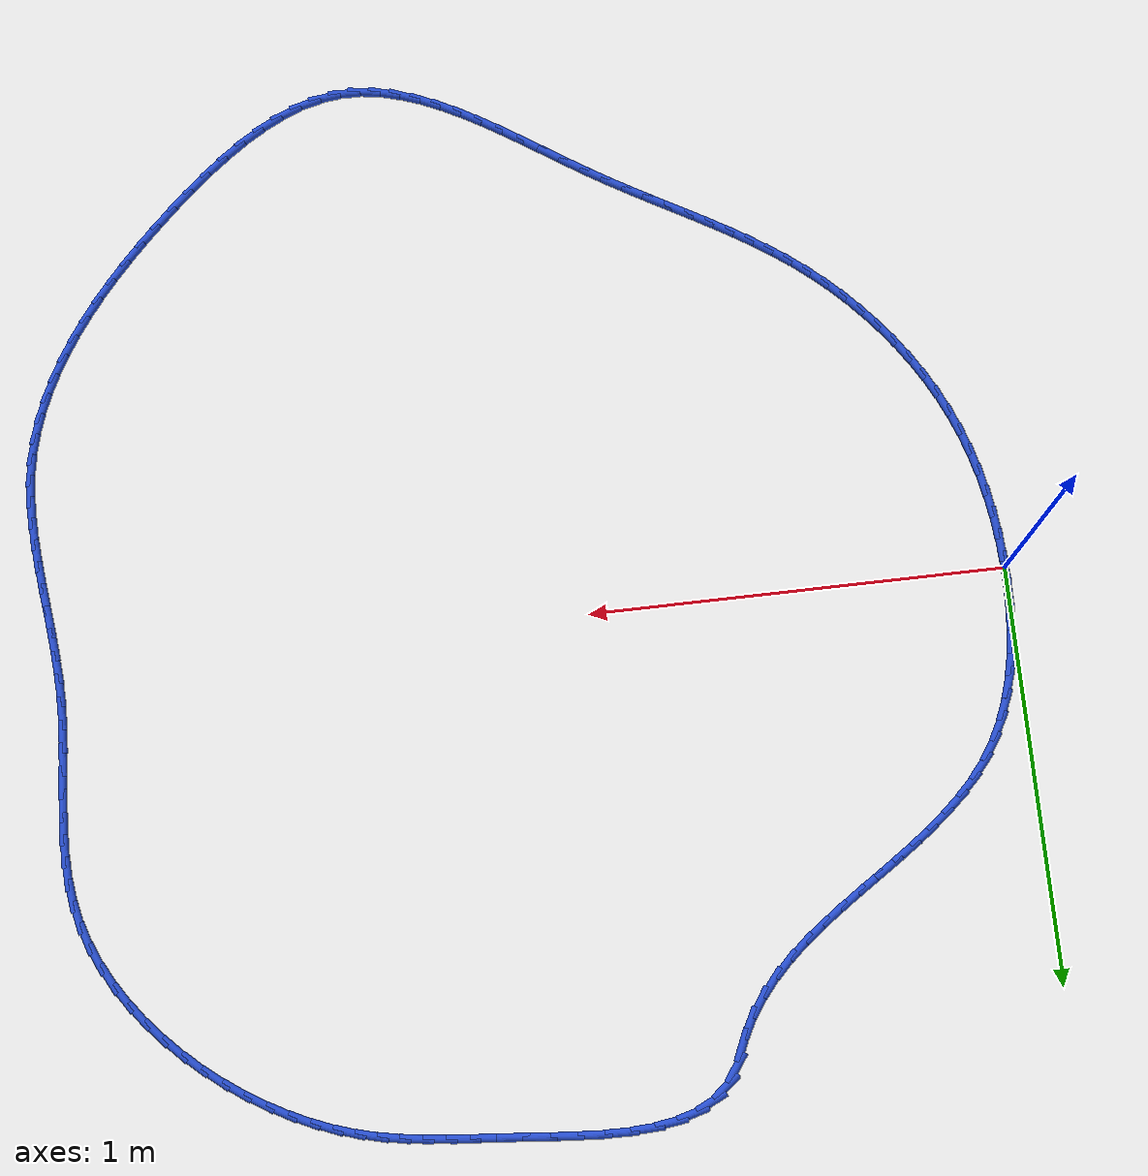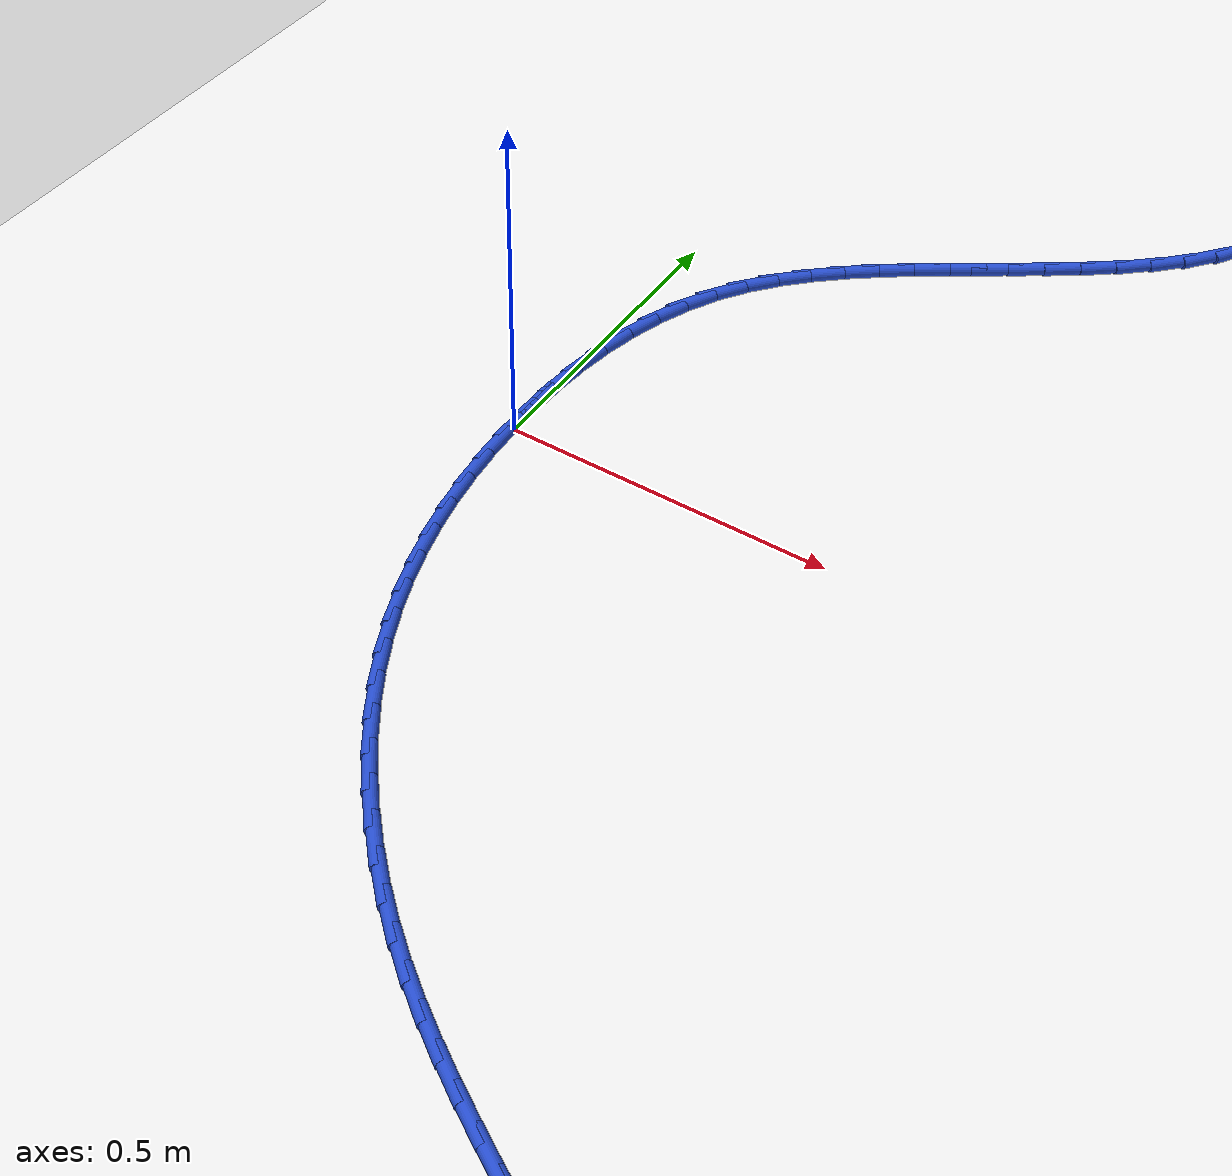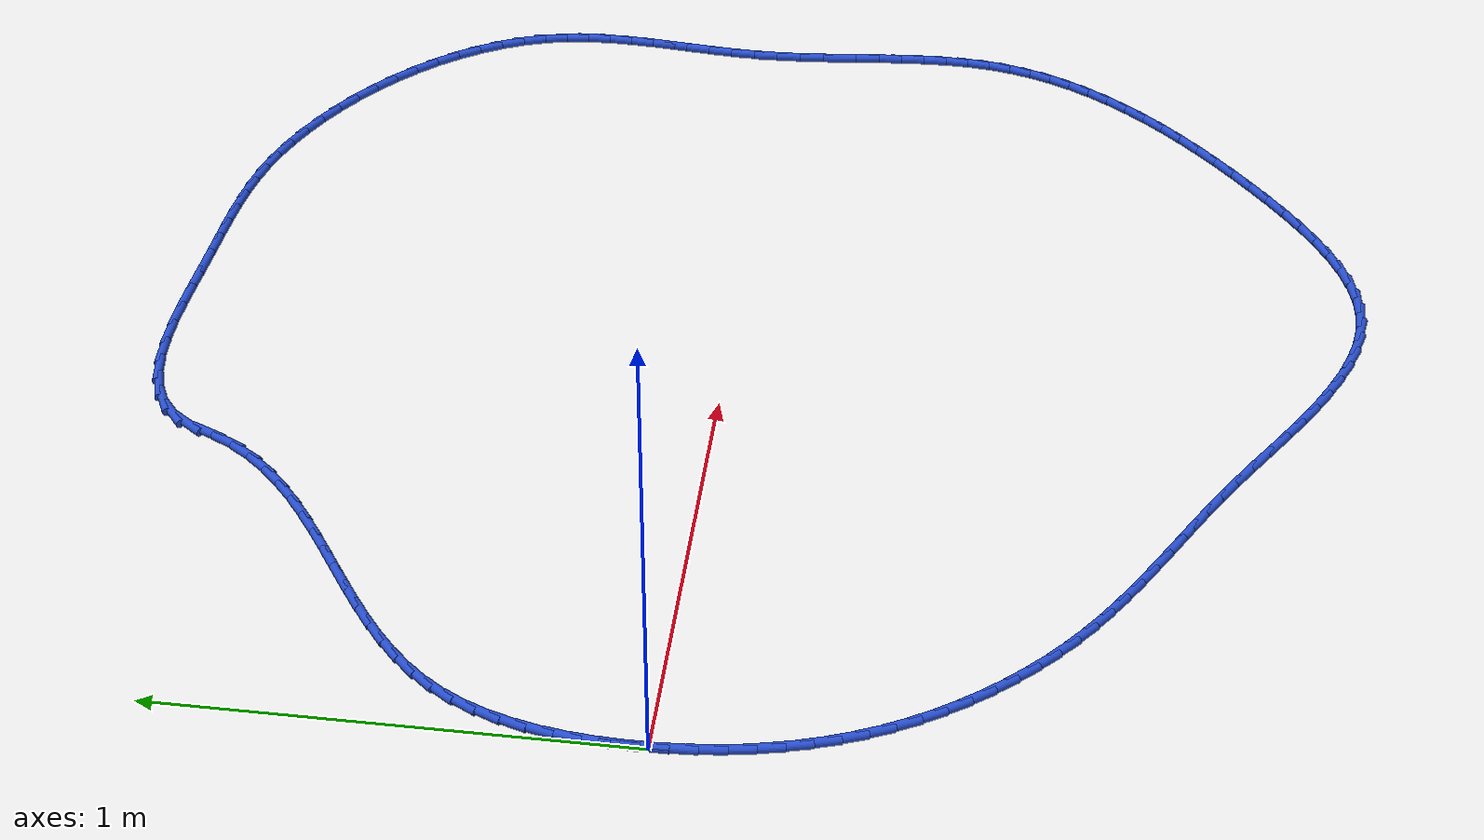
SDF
<sdf version="1.6">
 <world name="default">
  <light name="sun" type="directional">
   <pose>0 0 10 0 -0 0</pose>
   <diffuse>0.8 0.8 0.8 1</diffuse>
   <specular>0.2 0.2 0.2 1</specular>
   <attenuation>
    <range>1000</range>
    <constant>0.9</constant>
    <linear>0.01</linear>
    <quadratic>0.001</quadratic>
   </attenuation>
   <direction>-0.5 0.1 -0.9</direction>
  </light>
  <model name="ground_plane">
   <static>1</static>
   <link name="link">
    <collision name="collision">
     <geometry><plane><normal>0 0 1</normal><size>100 100</size></plane></geometry>
     <surface><friction><ode><mu>100</mu><mu2>50</mu2></ode></friction></surface>
    </collision>
    <visual name="visual">
     <cast_shadows>0</cast_shadows>
     <geometry><plane><normal>0 0 1</normal><size>100 100</size></plane></geometry>
     <material>
      <script><uri>file://media/materials/scripts/gazebo.material</uri><name>Gazebo/WhiteGlow</name></script>
     </material>
    </visual>
   </link>
  </model>
  <gravity>0 0 -9.8</gravity>
  <magnetic_field>6e-06 2.3e-05 -4.2e-05</magnetic_field>
  <atmosphere type="adiabatic"/>
  <physics name="default_physics" default="0" type="ode">
   <max_step_size>0.001</max_step_size>
   <real_time_factor>1</real_time_factor>
   <real_time_update_rate>1000</real_time_update_rate>
  </physics>
  <scene><ambient>0.4 0.4 0.4 1</ambient><background>0.7 0.7 0.7 1</background><shadows>1</shadows></scene>
  <spherical_coordinates>
   <surface_model>EARTH_WGS84</surface_model>
   <latitude_deg>0</latitude_deg>
   <longitude_deg>0</longitude_deg>
   <elevation>0</elevation>
   <heading_deg>0</heading_deg>
  </spherical_coordinates>
  <model name="line">
   <link name="link_0">
    <pose>-6.938893903907228e-18 -1.3877787807814457e-16 0.01 0 1.57 1.5702225282403262</pose>
    <collision name="collision">
     <geometry><cylinder><radius>0.01</radius><length>0.08</length></cylinder></geometry>
    </collision>
    <visual name="visual">
     <material>
      <script><name>Gazebo/Blue</name><uri>file://media/materials/scripts/gazebo.material</uri></script>
     </material>
     <geometry><cylinder><radius>0.01</radius><length>0.08</length></cylinder></geometry>
    </visual>
   </link>
   <link name="link_1">
    <pose>3.2122297887926364e-05 0.05598183213727158 0.01 0 1.57 1.5219617204032692</pose>
    <collision name="collision">
     <geometry><cylinder><radius>0.01</radius><length>0.08</length></cylinder></geometry>
    </collision>
    <visual name="visual">
     <material>
      <script><name>Gazebo/Blue</name><uri>file://media/materials/scripts/gazebo.material</uri></script>
     </material>
     <geometry><cylinder><radius>0.01</radius><length>0.08</length></cylinder></geometry>
    </visual>
   </link>
   <link name="link_2">
    <pose>0.0027720591368958205 0.1120436827521187 0.01 0 1.57 1.4680645423843748</pose>
    <collision name="collision">
     <geometry><cylinder><radius>0.01</radius><length>0.08</length></cylinder></geometry>
    </collision>
    <visual name="visual">
     <material>
      <script><name>Gazebo/Blue</name><uri>file://media/materials/scripts/gazebo.material</uri></script>
     </material>
     <geometry><cylinder><radius>0.01</radius><length>0.08</length></cylinder></geometry>
    </visual>
   </link>
   <link name="link_3">
    <pose>0.008510602290415246 0.1677065053002968 0.01 0 1.57 1.4074748132549735</pose>
    <collision name="collision">
     <geometry><cylinder><radius>0.01</radius><length>0.08</length></cylinder></geometry>
    </collision>
    <visual name="visual">
     <material>
      <script><name>Gazebo/Blue</name><uri>file://media/materials/scripts/gazebo.material</uri></script>
     </material>
     <geometry><cylinder><radius>0.01</radius><length>0.08</length></cylinder></geometry>
    </visual>
   </link>
   <link name="link_4">
    <pose>0.017538543531837758 0.22249125323756133 0.01 0 1.57 1.3390508978373714</pose>
    <collision name="collision">
     <geometry><cylinder><radius>0.01</radius><length>0.08</length></cylinder></geometry>
    </collision>
    <visual name="visual">
     <material>
      <script><name>Gazebo/Blue</name><uri>file://media/materials/scripts/gazebo.material</uri></script>
     </material>
     <geometry><cylinder><radius>0.01</radius><length>0.08</length></cylinder></geometry>
    </visual>
   </link>
   <link name="link_5">
    <pose>0.030146674634554928 0.2759188800196679 0.01 0 1.57 1.261623660727146</pose>
    <collision name="collision">
     <geometry><cylinder><radius>0.01</radius><length>0.08</length></cylinder></geometry>
    </collision>
    <visual name="visual">
     <material>
      <script><name>Gazebo/Blue</name><uri>file://media/materials/scripts/gazebo.material</uri></script>
     </material>
     <geometry><cylinder><radius>0.01</radius><length>0.08</length></cylinder></geometry>
    </visual>
   </link>
   <link name="link_6">
    <pose>0.046625787371958355 0.3275103391023724 0.01 0 1.57 1.1741198629882972</pose>
    <collision name="collision">
     <geometry><cylinder><radius>0.01</radius><length>0.08</length></cylinder></geometry>
    </collision>
    <visual name="visual">
     <material>
      <script><name>Gazebo/Blue</name><uri>file://media/materials/scripts/gazebo.material</uri></script>
     </material>
     <geometry><cylinder><radius>0.01</radius><length>0.08</length></cylinder></geometry>
    </visual>
   </link>
   <link name="link_7">
    <pose>0.06726667351743955 0.37678658394142994 0.01 0 1.57 1.0757766695661761</pose>
    <collision name="collision">
     <geometry><cylinder><radius>0.01</radius><length>0.08</length></cylinder></geometry>
    </collision>
    <visual name="visual">
     <material>
      <script><name>Gazebo/Blue</name><uri>file://media/materials/scripts/gazebo.material</uri></script>
     </material>
     <geometry><cylinder><radius>0.01</radius><length>0.08</length></cylinder></geometry>
    </visual>
   </link>
   <link name="link_8">
    <pose>0.09236012484439016 0.4232685679925963 0.01 0 1.57 0.9682542700632496</pose>
    <collision name="collision">
     <geometry><cylinder><radius>0.01</radius><length>0.08</length></cylinder></geometry>
    </collision>
    <visual name="visual">
     <material>
      <script><name>Gazebo/Blue</name><uri>file://media/materials/scripts/gazebo.material</uri></script>
     </material>
     <geometry><cylinder><radius>0.01</radius><length>0.08</length></cylinder></geometry>
    </visual>
   </link>
   <link name="link_9">
    <pose>0.12212934081932303 0.4665456296009552 0.01 0 1.57 0.8677020030502103</pose>
    <collision name="collision">
     <geometry><cylinder><radius>0.01</radius><length>0.08</length></cylinder></geometry>
    </collision>
    <visual name="visual">
     <material>
      <script><name>Gazebo/Blue</name><uri>file://media/materials/scripts/gazebo.material</uri></script>
     </material>
     <geometry><cylinder><radius>0.01</radius><length>0.08</length></cylinder></geometry>
    </visual>
   </link>
   <link name="link_10">
    <pose>0.1562314809479822 0.5067797844155647 0.01 0 1.57 0.7831304092725138</pose>
    <collision name="collision">
     <geometry><cylinder><radius>0.01</radius><length>0.08</length></cylinder></geometry>
    </collision>
    <visual name="visual">
     <material>
      <script><name>Gazebo/Blue</name><uri>file://media/materials/scripts/gazebo.material</uri></script>
     </material>
     <geometry><cylinder><radius>0.01</radius><length>0.08</length></cylinder></geometry>
    </visual>
   </link>
   <link name="link_11">
    <pose>0.19404142945407982 0.5444186333068378 0.01 0 1.57 0.7148547844319686</pose>
    <collision name="collision">
     <geometry><cylinder><radius>0.01</radius><length>0.08</length></cylinder></geometry>
    </collision>
    <visual name="visual">
     <material>
      <script><name>Gazebo/Blue</name><uri>file://media/materials/scripts/gazebo.material</uri></script>
     </material>
     <geometry><cylinder><radius>0.01</radius><length>0.08</length></cylinder></geometry>
    </visual>
   </link>
   <link name="link_12">
    <pose>0.2349319980802108 0.5799118739280671 0.01 0 1.57 0.6622686260626698</pose>
    <collision name="collision">
     <geometry><cylinder><radius>0.01</radius><length>0.08</length></cylinder></geometry>
    </collision>
    <visual name="visual">
     <material>
      <script><name>Gazebo/Blue</name><uri>file://media/materials/scripts/gazebo.material</uri></script>
     </material>
     <geometry><cylinder><radius>0.01</radius><length>0.08</length></cylinder></geometry>
    </visual>
   </link>
   <link name="link_13">
    <pose>0.27827599856897034 0.613709203932545 0.01 0 1.57 0.6244390640483001</pose>
    <collision name="collision">
     <geometry><cylinder><radius>0.01</radius><length>0.08</length></cylinder></geometry>
    </collision>
    <visual name="visual">
     <material>
      <script><name>Gazebo/Blue</name><uri>file://media/materials/scripts/gazebo.material</uri></script>
     </material>
     <geometry><cylinder><radius>0.01</radius><length>0.08</length></cylinder></geometry>
    </visual>
   </link>
   <link name="link_14">
    <pose>0.32344624266295324 0.6462603209735643 0.01 0 1.57 0.6004649058718042</pose>
    <collision name="collision">
     <geometry><cylinder><radius>0.01</radius><length>0.08</length></cylinder></geometry>
    </collision>
    <visual name="visual">
     <material>
      <script><name>Gazebo/Blue</name><uri>file://media/materials/scripts/gazebo.material</uri></script>
     </material>
     <geometry><cylinder><radius>0.01</radius><length>0.08</length></cylinder></geometry>
    </visual>
   </link>
   <link name="link_15">
    <pose>0.3698155421047546 0.6780149227044174 0.01 0 1.57 0.5896772273931061</pose>
    <collision name="collision">
     <geometry><cylinder><radius>0.01</radius><length>0.08</length></cylinder></geometry>
    </collision>
    <visual name="visual">
     <material>
      <script><name>Gazebo/Blue</name><uri>file://media/materials/scripts/gazebo.material</uri></script>
     </material>
     <geometry><cylinder><radius>0.01</radius><length>0.08</length></cylinder></geometry>
    </visual>
   </link>
   <link name="link_16">
    <pose>0.41675670863696973 0.7094227067783972 0.01 0 1.57 0.5917354304771028</pose>
    <collision name="collision">
     <geometry><cylinder><radius>0.01</radius><length>0.08</length></cylinder></geometry>
    </collision>
    <visual name="visual">
     <material>
      <script><name>Gazebo/Blue</name><uri>file://media/materials/scripts/gazebo.material</uri></script>
     </material>
     <geometry><cylinder><radius>0.01</radius><length>0.08</length></cylinder></geometry>
    </visual>
   </link>
   <link name="link_17">
    <pose>0.46364255400219306 0.7409333708487956 0.01 0 1.57 0.6066603906495799</pose>
    <collision name="collision">
     <geometry><cylinder><radius>0.01</radius><length>0.08</length></cylinder></geometry>
    </collision>
    <visual name="visual">
     <material>
      <script><name>Gazebo/Blue</name><uri>file://media/materials/scripts/gazebo.material</uri></script>
     </material>
     <geometry><cylinder><radius>0.01</radius><length>0.08</length></cylinder></geometry>
    </visual>
   </link>
   <link name="link_18">
    <pose>0.50984588994302 0.7729966125689057 0.01 0 1.57 0.6348245065593896</pose>
    <collision name="collision">
     <geometry><cylinder><radius>0.01</radius><length>0.08</length></cylinder></geometry>
    </collision>
    <visual name="visual">
     <material>
      <script><name>Gazebo/Blue</name><uri>file://media/materials/scripts/gazebo.material</uri></script>
     </material>
     <geometry><cylinder><radius>0.01</radius><length>0.08</length></cylinder></geometry>
    </visual>
   </link>
   <link name="link_19">
    <pose>0.5547395282020455 0.8060621295920198 0.01 0 1.57 0.6768960546514915</pose>
    <collision name="collision">
     <geometry><cylinder><radius>0.01</radius><length>0.08</length></cylinder></geometry>
    </collision>
    <visual name="visual">
     <material>
      <script><name>Gazebo/Blue</name><uri>file://media/materials/scripts/gazebo.material</uri></script>
     </material>
     <geometry><cylinder><radius>0.01</radius><length>0.08</length></cylinder></geometry>
    </visual>
   </link>
   <link name="link_20">
    <pose>0.5976962805218647 0.8405796195714306 0.01 0 1.57 0.7337136986147049</pose>
    <collision name="collision">
     <geometry><cylinder><radius>0.01</radius><length>0.08</length></cylinder></geometry>
    </collision>
    <visual name="visual">
     <material>
      <script><name>Gazebo/Blue</name><uri>file://media/materials/scripts/gazebo.material</uri></script>
     </material>
     <geometry><cylinder><radius>0.01</radius><length>0.08</length></cylinder></geometry>
    </visual>
   </link>
   <link name="link_21">
    <pose>0.6380889586450723 0.8769987801604304 0.01 0 1.57 0.8060490777768412</pose>
    <collision name="collision">
     <geometry><cylinder><radius>0.01</radius><length>0.08</length></cylinder></geometry>
    </collision>
    <visual name="visual">
     <material>
      <script><name>Gazebo/Blue</name><uri>file://media/materials/scripts/gazebo.material</uri></script>
     </material>
     <geometry><cylinder><radius>0.01</radius><length>0.08</length></cylinder></geometry>
    </visual>
   </link>
   <link name="link_22">
    <pose>0.6752903743142635 0.9157693090123119 0.01 0 1.57 0.8942145418022549</pose>
    <collision name="collision">
     <geometry><cylinder><radius>0.01</radius><length>0.08</length></cylinder></geometry>
    </collision>
    <visual name="visual">
     <material>
      <script><name>Gazebo/Blue</name><uri>file://media/materials/scripts/gazebo.material</uri></script>
     </material>
     <geometry><cylinder><radius>0.01</radius><length>0.08</length></cylinder></geometry>
    </visual>
   </link>
   <link name="link_23">
    <pose>0.7086733392720335 0.9573409037803677 0.01 0 1.57 0.9975202933428055</pose>
    <collision name="collision">
     <geometry><cylinder><radius>0.01</radius><length>0.08</length></cylinder></geometry>
    </collision>
    <visual name="visual">
     <material>
      <script><name>Gazebo/Blue</name><uri>file://media/materials/scripts/gazebo.material</uri></script>
     </material>
     <geometry><cylinder><radius>0.01</radius><length>0.08</length></cylinder></geometry>
    </visual>
   </link>
   <link name="link_24">
    <pose>0.7376106652609772 1.0021632621178906 0.01 0 1.57 1.1136810013321163</pose>
    <collision name="collision">
     <geometry><cylinder><radius>0.01</radius><length>0.08</length></cylinder></geometry>
    </collision>
    <visual name="visual">
     <material>
      <script><name>Gazebo/Blue</name><uri>file://media/materials/scripts/gazebo.material</uri></script>
     </material>
     <geometry><cylinder><radius>0.01</radius><length>0.08</length></cylinder></geometry>
    </visual>
   </link>
   <link name="link_25">
    <pose>0.7614765124189773 1.0506847787572993 0.01 0 1.57 1.1640529269467912</pose>
    <collision name="collision">
     <geometry><cylinder><radius>0.01</radius><length>0.08</length></cylinder></geometry>
    </collision>
    <visual name="visual">
     <material>
      <script><name>Gazebo/Blue</name><uri>file://media/materials/scripts/gazebo.material</uri></script>
     </material>
     <geometry><cylinder><radius>0.01</radius><length>0.08</length></cylinder></geometry>
    </visual>
   </link>
   <link name="link_26">
    <pose>0.7828362127023534 1.1002702983695678 0.01 0 1.57 0.9549133107945891</pose>
    <collision name="collision">
     <geometry><cylinder><radius>0.01</radius><length>0.08</length></cylinder></geometry>
    </collision>
    <visual name="visual">
     <material>
      <script><name>Gazebo/Blue</name><uri>file://media/materials/scripts/gazebo.material</uri></script>
     </material>
     <geometry><cylinder><radius>0.01</radius><length>0.08</length></cylinder></geometry>
    </visual>
   </link>
   <link name="link_27">
    <pose>0.8117233404273001 1.1410879349267236 0.01 0 1.57 0.6807663889096673</pose>
    <collision name="collision">
     <geometry><cylinder><radius>0.01</radius><length>0.08</length></cylinder></geometry>
    </collision>
    <visual name="visual">
     <material>
      <script><name>Gazebo/Blue</name><uri>file://media/materials/scripts/gazebo.material</uri></script>
     </material>
     <geometry><cylinder><radius>0.01</radius><length>0.08</length></cylinder></geometry>
    </visual>
   </link>
   <link name="link_28">
    <pose>0.849546079573539 1.1717216953593381 0.01 0 1.57 0.4457332259470823</pose>
    <collision name="collision">
     <geometry><cylinder><radius>0.01</radius><length>0.08</length></cylinder></geometry>
    </collision>
    <visual name="visual">
     <material>
      <script><name>Gazebo/Blue</name><uri>file://media/materials/scripts/gazebo.material</uri></script>
     </material>
     <geometry><cylinder><radius>0.01</radius><length>0.08</length></cylinder></geometry>
    </visual>
   </link>
   <link name="link_29">
    <pose>0.8949709551513052 1.193425858319838 0.01 0 1.57 0.2650022575327565</pose>
    <collision name="collision">
     <geometry><cylinder><radius>0.01</radius><length>0.08</length></cylinder></geometry>
    </collision>
    <visual name="visual">
     <material>
      <script><name>Gazebo/Blue</name><uri>file://media/materials/scripts/gazebo.material</uri></script>
     </material>
     <geometry><cylinder><radius>0.01</radius><length>0.08</length></cylinder></geometry>
    </visual>
   </link>
   <link name="link_30">
    <pose>0.9466644879328847 1.2074547065882542 0.01 0 1.57 0.1335459545853411</pose>
    <collision name="collision">
     <geometry><cylinder><radius>0.01</radius><length>0.08</length></cylinder></geometry>
    </collision>
    <visual name="visual">
     <material>
      <script><name>Gazebo/Blue</name><uri>file://media/materials/scripts/gazebo.material</uri></script>
     </material>
     <geometry><cylinder><radius>0.01</radius><length>0.08</length></cylinder></geometry>
    </visual>
   </link>
   <link name="link_31">
    <pose>1.0032931986905642 1.2150625229446157 0.01 0 1.57 0.0405066478310615</pose>
    <collision name="collision">
     <geometry><cylinder><radius>0.01</radius><length>0.08</length></cylinder></geometry>
    </collision>
    <visual name="visual">
     <material>
      <script><name>Gazebo/Blue</name><uri>file://media/materials/scripts/gazebo.material</uri></script>
     </material>
     <geometry><cylinder><radius>0.01</radius><length>0.08</length></cylinder></geometry>
    </visual>
   </link>
   <link name="link_32">
    <pose>1.0635236081966288 1.217503590168953 0.01 0 1.57 -0.023538554221004135</pose>
    <collision name="collision">
     <geometry><cylinder><radius>0.01</radius><length>0.08</length></cylinder></geometry>
    </collision>
    <visual name="visual">
     <material>
      <script><name>Gazebo/Blue</name><uri>file://media/materials/scripts/gazebo.material</uri></script>
     </material>
     <geometry><cylinder><radius>0.01</radius><length>0.08</length></cylinder></geometry>
    </visual>
   </link>
   <link name="link_33">
    <pose>1.126022237223365 1.2160321910412966 0.01 0 1.57 -0.0650093727919637</pose>
    <collision name="collision">
     <geometry><cylinder><radius>0.01</radius><length>0.08</length></cylinder></geometry>
    </collision>
    <visual name="visual">
     <material>
      <script><name>Gazebo/Blue</name><uri>file://media/materials/scripts/gazebo.material</uri></script>
     </material>
     <geometry><cylinder><radius>0.01</radius><length>0.08</length></cylinder></geometry>
    </visual>
   </link>
   <link name="link_34">
    <pose>1.1894556065430593 1.2119026083416746 0.01 0 1.57 -0.08756035886712663</pose>
    <collision name="collision">
     <geometry><cylinder><radius>0.01</radius><length>0.08</length></cylinder></geometry>
    </collision>
    <visual name="visual">
     <material>
      <script><name>Gazebo/Blue</name><uri>file://media/materials/scripts/gazebo.material</uri></script>
     </material>
     <geometry><cylinder><radius>0.01</radius><length>0.08</length></cylinder></geometry>
    </visual>
   </link>
   <link name="link_35">
    <pose>1.2524902369279975 1.2063691248501192 0.01 0 1.57 -0.09244694729825857</pose>
    <collision name="collision">
     <geometry><cylinder><radius>0.01</radius><length>0.08</length></cylinder></geometry>
    </collision>
    <visual name="visual">
     <material>
      <script><name>Gazebo/Blue</name><uri>file://media/materials/scripts/gazebo.material</uri></script>
     </material>
     <geometry><cylinder><radius>0.01</radius><length>0.08</length></cylinder></geometry>
    </visual>
   </link>
   <link name="link_36">
    <pose>1.3137929698151114 1.2006856740142207 0.01 0 1.57 -0.08521738920645766</pose>
    <collision name="collision">
     <geometry><cylinder><radius>0.01</radius><length>0.08</length></cylinder></geometry>
    </collision>
    <visual name="visual">
     <material>
      <script><name>Gazebo/Blue</name><uri>file://media/materials/scripts/gazebo.material</uri></script>
     </material>
     <geometry><cylinder><radius>0.01</radius><length>0.08</length></cylinder></geometry>
    </visual>
   </link>
   <link name="link_37">
    <pose>1.3724245067854208 1.195677117583411 0.01 0 1.57 -0.08475441747929263</pose>
    <collision name="collision">
     <geometry><cylinder><radius>0.01</radius><length>0.08</length></cylinder></geometry>
    </collision>
    <visual name="visual">
     <material>
      <script><name>Gazebo/Blue</name><uri>file://media/materials/scripts/gazebo.material</uri></script>
     </material>
     <geometry><cylinder><radius>0.01</radius><length>0.08</length></cylinder></geometry>
    </visual>
   </link>
   <link name="link_38">
    <pose>1.428606067224941 1.1909040478632285 0.01 0 1.57 -0.09586782875110215</pose>
    <collision name="collision">
     <geometry><cylinder><radius>0.01</radius><length>0.08</length></cylinder></geometry>
    </collision>
    <visual name="visual">
     <material>
      <script><name>Gazebo/Blue</name><uri>file://media/materials/scripts/gazebo.material</uri></script>
     </material>
     <geometry><cylinder><radius>0.01</radius><length>0.08</length></cylinder></geometry>
    </visual>
   </link>
   <link name="link_39">
    <pose>1.4827715601830687 1.1856953527930372 0.01 0 1.57 -0.11953076735419567</pose>
    <collision name="collision">
     <geometry><cylinder><radius>0.01</radius><length>0.08</length></cylinder></geometry>
    </collision>
    <visual name="visual">
     <material>
      <script><name>Gazebo/Blue</name><uri>file://media/materials/scripts/gazebo.material</uri></script>
     </material>
     <geometry><cylinder><radius>0.01</radius><length>0.08</length></cylinder></geometry>
    </visual>
   </link>
   <link name="link_40">
    <pose>1.5353548947091977 1.1793799203122013 0.01 0 1.57 -0.1560698015272833</pose>
    <collision name="collision">
     <geometry><cylinder><radius>0.01</radius><length>0.08</length></cylinder></geometry>
    </collision>
    <visual name="visual">
     <material>
      <script><name>Gazebo/Blue</name><uri>file://media/materials/scripts/gazebo.material</uri></script>
     </material>
     <geometry><cylinder><radius>0.01</radius><length>0.08</length></cylinder></geometry>
    </visual>
   </link>
   <link name="link_41">
    <pose>1.5867899798527234 1.1712866383600833 0.01 0 1.57 -0.20493091976538488</pose>
    <collision name="collision">
     <geometry><cylinder><radius>0.01</radius><length>0.08</length></cylinder></geometry>
    </collision>
    <visual name="visual">
     <material>
      <script><name>Gazebo/Blue</name><uri>file://media/materials/scripts/gazebo.material</uri></script>
     </material>
     <geometry><cylinder><radius>0.01</radius><length>0.08</length></cylinder></geometry>
    </visual>
   </link>
   <link name="link_42">
    <pose>1.63751072466304 1.1607443948760483 0.01 0 1.57 -0.2645142195695105</pose>
    <collision name="collision">
     <geometry><cylinder><radius>0.01</radius><length>0.08</length></cylinder></geometry>
    </collision>
    <visual name="visual">
     <material>
      <script><name>Gazebo/Blue</name><uri>file://media/materials/scripts/gazebo.material</uri></script>
     </material>
     <geometry><cylinder><radius>0.01</radius><length>0.08</length></cylinder></geometry>
    </visual>
   </link>
   <link name="link_43">
    <pose>1.687951038189544 1.1470820777994597 0.01 0 1.57 -0.3314979268367801</pose>
    <collision name="collision">
     <geometry><cylinder><radius>0.01</radius><length>0.08</length></cylinder></geometry>
    </collision>
    <visual name="visual">
     <material>
      <script><name>Gazebo/Blue</name><uri>file://media/materials/scripts/gazebo.material</uri></script>
     </material>
     <geometry><cylinder><radius>0.01</radius><length>0.08</length></cylinder></geometry>
    </visual>
   </link>
   <link name="link_44">
    <pose>1.738491869899307 1.12968595402742 0.01 0 1.57 -0.3973964685917838</pose>
    <collision name="collision">
     <geometry><cylinder><radius>0.01</radius><length>0.08</length></cylinder></geometry>
    </collision>
    <visual name="visual">
     <material>
      <script><name>Gazebo/Blue</name><uri>file://media/materials/scripts/gazebo.material</uri></script>
     </material>
     <geometry><cylinder><radius>0.01</radius><length>0.08</length></cylinder></geometry>
    </visual>
   </link>
   <link name="link_45">
    <pose>1.7890196943327938 1.1084780283664384 0.01 0 1.57 -0.4594868693141899</pose>
    <collision name="collision">
     <geometry><cylinder><radius>0.01</radius><length>0.08</length></cylinder></geometry>
    </collision>
    <visual name="visual">
     <material>
      <script><name>Gazebo/Blue</name><uri>file://media/materials/scripts/gazebo.material</uri></script>
     </material>
     <geometry><cylinder><radius>0.01</radius><length>0.08</length></cylinder></geometry>
    </visual>
   </link>
   <link name="link_46">
    <pose>1.8391514358935992 1.083672349201045 0.01 0 1.57 -0.5189401493082975</pose>
    <collision name="collision">
     <geometry><cylinder><radius>0.01</radius><length>0.08</length></cylinder></geometry>
    </collision>
    <visual name="visual">
     <material>
      <script><name>Gazebo/Blue</name><uri>file://media/materials/scripts/gazebo.material</uri></script>
     </material>
     <geometry><cylinder><radius>0.01</radius><length>0.08</length></cylinder></geometry>
    </visual>
   </link>
   <link name="link_47">
    <pose>1.8885013043271217 1.055485906106975 0.01 0 1.57 -0.5768388179129491</pose>
    <collision name="collision">
     <geometry><cylinder><radius>0.01</radius><length>0.08</length></cylinder></geometry>
    </collision>
    <visual name="visual">
     <material>
      <script><name>Gazebo/Blue</name><uri>file://media/materials/scripts/gazebo.material</uri></script>
     </material>
     <geometry><cylinder><radius>0.01</radius><length>0.08</length></cylinder></geometry>
    </visual>
   </link>
   <link name="link_48">
    <pose>1.9366835093787633 1.0241356886599629 0.01 0 1.57 -0.6341779881410391</pose>
    <collision name="collision">
     <geometry><cylinder><radius>0.01</radius><length>0.08</length></cylinder></geometry>
    </collision>
    <visual name="visual">
     <material>
      <script><name>Gazebo/Blue</name><uri>file://media/materials/scripts/gazebo.material</uri></script>
     </material>
     <geometry><cylinder><radius>0.01</radius><length>0.08</length></cylinder></geometry>
    </visual>
   </link>
   <link name="link_49">
    <pose>1.983312260793924 0.9898386864357434 0.01 0 1.57 -0.6918994678060304</pose>
    <collision name="collision">
     <geometry><cylinder><radius>0.01</radius><length>0.08</length></cylinder></geometry>
    </collision>
    <visual name="visual">
     <material>
      <script><name>Gazebo/Blue</name><uri>file://media/materials/scripts/gazebo.material</uri></script>
     </material>
     <geometry><cylinder><radius>0.01</radius><length>0.08</length></cylinder></geometry>
    </visual>
   </link>
   <link name="link_50">
    <pose>2.0280017683180036 0.9528118890100509 0.01 0 1.57 -0.7509218450971212</pose>
    <collision name="collision">
     <geometry><cylinder><radius>0.01</radius><length>0.08</length></cylinder></geometry>
    </collision>
    <visual name="visual">
     <material>
      <script><name>Gazebo/Blue</name><uri>file://media/materials/scripts/gazebo.material</uri></script>
     </material>
     <geometry><cylinder><radius>0.01</radius><length>0.08</length></cylinder></geometry>
    </visual>
   </link>
   <link name="link_51">
    <pose>2.070366241696404 0.913272285958621 0.01 0 1.57 -0.8121655455220732</pose>
    <collision name="collision">
     <geometry><cylinder><radius>0.01</radius><length>0.08</length></cylinder></geometry>
    </collision>
    <visual name="visual">
     <material>
      <script><name>Gazebo/Blue</name><uri>file://media/materials/scripts/gazebo.material</uri></script>
     </material>
     <geometry><cylinder><radius>0.01</radius><length>0.08</length></cylinder></geometry>
    </visual>
   </link>
   <link name="link_52">
    <pose>2.1100198906745256 0.8714368668571877 0.01 0 1.57 -0.8765712412404038</pose>
    <collision name="collision">
     <geometry><cylinder><radius>0.01</radius><length>0.08</length></cylinder></geometry>
    </collision>
    <visual name="visual">
     <material>
      <script><name>Gazebo/Blue</name><uri>file://media/materials/scripts/gazebo.material</uri></script>
     </material>
     <geometry><cylinder><radius>0.01</radius><length>0.08</length></cylinder></geometry>
    </visual>
   </link>
   <link name="link_53">
    <pose>2.1465769249977686 0.8275226212814862 0.01 0 1.57 -0.9451085197990835</pose>
    <collision name="collision">
     <geometry><cylinder><radius>0.01</radius><length>0.08</length></cylinder></geometry>
    </collision>
    <visual name="visual">
     <material>
      <script><name>Gazebo/Blue</name><uri>file://media/materials/scripts/gazebo.material</uri></script>
     </material>
     <geometry><cylinder><radius>0.01</radius><length>0.08</length></cylinder></geometry>
    </visual>
   </link>
   <link name="link_54">
    <pose>2.179651554411533 0.7817465388072509 0.01 0 1.57 -1.0187693902711445</pose>
    <collision name="collision">
     <geometry><cylinder><radius>0.01</radius><length>0.08</length></cylinder></geometry>
    </collision>
    <visual name="visual">
     <material>
      <script><name>Gazebo/Blue</name><uri>file://media/materials/scripts/gazebo.material</uri></script>
     </material>
     <geometry><cylinder><radius>0.01</radius><length>0.08</length></cylinder></geometry>
    </visual>
   </link>
   <link name="link_55">
    <pose>2.2088579886612196 0.7343256090102159 0.01 0 1.57 -1.0985381689861873</pose>
    <collision name="collision">
     <geometry><cylinder><radius>0.01</radius><length>0.08</length></cylinder></geometry>
    </collision>
    <visual name="visual">
     <material>
      <script><name>Gazebo/Blue</name><uri>file://media/materials/scripts/gazebo.material</uri></script>
     </material>
     <geometry><cylinder><radius>0.01</radius><length>0.08</length></cylinder></geometry>
    </visual>
   </link>
   <link name="link_56">
    <pose>2.2338104374922305 0.6854768214661173 0.01 0 1.57 -1.1853263015811197</pose>
    <collision name="collision">
     <geometry><cylinder><radius>0.01</radius><length>0.08</length></cylinder></geometry>
    </collision>
    <visual name="visual">
     <material>
      <script><name>Gazebo/Blue</name><uri>file://media/materials/scripts/gazebo.material</uri></script>
     </material>
     <geometry><cylinder><radius>0.01</radius><length>0.08</length></cylinder></geometry>
    </visual>
   </link>
   <link name="link_57">
    <pose>2.254123110649965 0.6354171657506887 0.01 0 1.57 -1.2798598995778012</pose>
    <collision name="collision">
     <geometry><cylinder><radius>0.01</radius><length>0.08</length></cylinder></geometry>
    </collision>
    <visual name="visual">
     <material>
      <script><name>Gazebo/Blue</name><uri>file://media/materials/scripts/gazebo.material</uri></script>
     </material>
     <geometry><cylinder><radius>0.01</radius><length>0.08</length></cylinder></geometry>
    </visual>
   </link>
   <link name="link_58">
    <pose>2.2694102178798223 0.5843636314396653 0.01 0 1.57 -1.3795031104860749</pose>
    <collision name="collision">
     <geometry><cylinder><radius>0.01</radius><length>0.08</length></cylinder></geometry>
    </collision>
    <visual name="visual">
     <material>
      <script><name>Gazebo/Blue</name><uri>file://media/materials/scripts/gazebo.material</uri></script>
     </material>
     <geometry><cylinder><radius>0.01</radius><length>0.08</length></cylinder></geometry>
    </visual>
   </link>
   <link name="link_59">
    <pose>2.279451374925731 0.5325145465817072 0.01 0 1.57 -1.4682625775375797</pose>
    <collision name="collision">
     <geometry><cylinder><radius>0.01</radius><length>0.08</length></cylinder></geometry>
    </collision>
    <visual name="visual">
     <material>
      <script><name>Gazebo/Blue</name><uri>file://media/materials/scripts/gazebo.material</uri></script>
     </material>
     <geometry><cylinder><radius>0.01</radius><length>0.08</length></cylinder></geometry>
    </visual>
   </link>
   <link name="link_60">
    <pose>2.2848574660091914 0.4799744533934094 0.01 0 1.57 -1.5399068745585391</pose>
    <collision name="collision">
     <geometry><cylinder><radius>0.01</radius><length>0.08</length></cylinder></geometry>
    </collision>
    <visual name="visual">
     <material>
      <script><name>Gazebo/Blue</name><uri>file://media/materials/scripts/gazebo.material</uri></script>
     </material>
     <geometry><cylinder><radius>0.01</radius><length>0.08</length></cylinder></geometry>
    </visual>
   </link>
   <link name="link_61">
    <pose>2.2864999468527034 0.4268184957493223 0.01 0 1.57 1.5475294024090605</pose>
    <collision name="collision">
     <geometry><cylinder><radius>0.01</radius><length>0.08</length></cylinder></geometry>
    </collision>
    <visual name="visual">
     <material>
      <script><name>Gazebo/Blue</name><uri>file://media/materials/scripts/gazebo.material</uri></script>
     </material>
     <geometry><cylinder><radius>0.01</radius><length>0.08</length></cylinder></geometry>
    </visual>
   </link>
   <link name="link_62">
    <pose>2.2852503645656044 0.3731218072135017 0.01 0 1.57 1.510493599919556</pose>
    <collision name="collision">
     <geometry><cylinder><radius>0.01</radius><length>0.08</length></cylinder></geometry>
    </collision>
    <visual name="visual">
     <material>
      <script><name>Gazebo/Blue</name><uri>file://media/materials/scripts/gazebo.material</uri></script>
     </material>
     <geometry><cylinder><radius>0.01</radius><length>0.08</length></cylinder></geometry>
    </visual>
   </link>
   <link name="link_63">
    <pose>2.281980266257231 0.31895952135000183 0.01 0 1.57 1.489967416426141</pose>
    <collision name="collision">
     <geometry><cylinder><radius>0.01</radius><length>0.08</length></cylinder></geometry>
    </collision>
    <visual name="visual">
     <material>
      <script><name>Gazebo/Blue</name><uri>file://media/materials/scripts/gazebo.material</uri></script>
     </material>
     <geometry><cylinder><radius>0.01</radius><length>0.08</length></cylinder></geometry>
    </visual>
   </link>
   <link name="link_64">
    <pose>2.277561199036918 0.26440677172287835 0.01 0 1.57 1.4854084417152182</pose>
    <collision name="collision">
     <geometry><cylinder><radius>0.01</radius><length>0.08</length></cylinder></geometry>
    </collision>
    <visual name="visual">
     <material>
      <script><name>Gazebo/Blue</name><uri>file://media/materials/scripts/gazebo.material</uri></script>
     </material>
     <geometry><cylinder><radius>0.01</radius><length>0.08</length></cylinder></geometry>
    </visual>
   </link>
   <link name="link_65">
    <pose>2.2728647100140043 0.2095386918961859 0.01 0 1.57 1.4964915000347971</pose>
    <collision name="collision">
     <geometry><cylinder><radius>0.01</radius><length>0.08</length></cylinder></geometry>
    </collision>
    <visual name="visual">
     <material>
      <script><name>Gazebo/Blue</name><uri>file://media/materials/scripts/gazebo.material</uri></script>
     </material>
     <geometry><cylinder><radius>0.01</radius><length>0.08</length></cylinder></geometry>
    </visual>
   </link>
   <link name="link_66">
    <pose>2.2687623462978244 0.15443041543397884 0.01 0 1.57 1.5231296927421487</pose>
    <collision name="collision">
     <geometry><cylinder><radius>0.01</radius><length>0.08</length></cylinder></geometry>
    </collision>
    <visual name="visual">
     <material>
      <script><name>Gazebo/Blue</name><uri>file://media/materials/scripts/gazebo.material</uri></script>
     </material>
     <geometry><cylinder><radius>0.01</radius><length>0.08</length></cylinder></geometry>
    </visual>
   </link>
   <link name="link_67">
    <pose>2.266125654997715 0.0991570759003132 0.01 0 1.57 1.5650289437432428</pose>
    <collision name="collision">
     <geometry><cylinder><radius>0.01</radius><length>0.08</length></cylinder></geometry>
    </collision>
    <visual name="visual">
     <material>
      <script><name>Gazebo/Blue</name><uri>file://media/materials/scripts/gazebo.material</uri></script>
     </material>
     <geometry><cylinder><radius>0.01</radius><length>0.08</length></cylinder></geometry>
    </visual>
   </link>
   <link name="link_68">
    <pose>2.2658063513145645 0.04379398661334496 0.01 0 1.57 -1.5314216455627647</pose>
    <collision name="collision">
     <geometry><cylinder><radius>0.01</radius><length>0.08</length></cylinder></geometry>
    </collision>
    <visual name="visual">
     <material>
      <script><name>Gazebo/Blue</name><uri>file://media/materials/scripts/gazebo.material</uri></script>
     </material>
     <geometry><cylinder><radius>0.01</radius><length>0.08</length></cylinder></geometry>
    </visual>
   </link>
   <link name="link_69">
    <pose>2.2679877125991506 -0.011577480466162785 0.01 0 1.57 -1.4976416497448057</pose>
    <collision name="collision">
     <geometry><cylinder><radius>0.01</radius><length>0.08</length></cylinder></geometry>
    </collision>
    <visual name="visual">
     <material>
      <script><name>Gazebo/Blue</name><uri>file://media/materials/scripts/gazebo.material</uri></script>
     </material>
     <geometry><cylinder><radius>0.01</radius><length>0.08</length></cylinder></geometry>
    </visual>
   </link>
   <link name="link_70">
    <pose>2.272039746151987 -0.06686858199269607 0.01 0 1.57 -1.4759544008531393</pose>
    <collision name="collision">
     <geometry><cylinder><radius>0.01</radius><length>0.08</length></cylinder></geometry>
    </collision>
    <visual name="visual">
     <material>
      <script><name>Gazebo/Blue</name><uri>file://media/materials/scripts/gazebo.material</uri></script>
     </material>
     <geometry><cylinder><radius>0.01</radius><length>0.08</length></cylinder></geometry>
    </visual>
   </link>
   <link name="link_71">
    <pose>2.277283311221189 -0.12199012914853248 0.01 0 1.57 -1.4662632966866773</pose>
    <collision name="collision">
     <geometry><cylinder><radius>0.01</radius><length>0.08</length></cylinder></geometry>
    </collision>
    <visual name="visual">
     <material>
      <script><name>Gazebo/Blue</name><uri>file://media/materials/scripts/gazebo.material</uri></script>
     </material>
     <geometry><cylinder><radius>0.01</radius><length>0.08</length></cylinder></geometry>
    </visual>
   </link>
   <link name="link_72">
    <pose>2.28303926705487 -0.17685293311595088 0.01 0 1.57 -1.4686270590977248</pose>
    <collision name="collision">
     <geometry><cylinder><radius>0.01</radius><length>0.08</length></cylinder></geometry>
    </collision>
    <visual name="visual">
     <material>
      <script><name>Gazebo/Blue</name><uri>file://media/materials/scripts/gazebo.material</uri></script>
     </material>
     <geometry><cylinder><radius>0.01</radius><length>0.08</length></cylinder></geometry>
    </visual>
   </link>
   <link name="link_73">
    <pose>2.288628472901146 -0.23136780507723054 0.01 0 1.57 -1.483307358704458</pose>
    <collision name="collision">
     <geometry><cylinder><radius>0.01</radius><length>0.08</length></cylinder></geometry>
    </collision>
    <visual name="visual">
     <material>
      <script><name>Gazebo/Blue</name><uri>file://media/materials/scripts/gazebo.material</uri></script>
     </material>
     <geometry><cylinder><radius>0.01</radius><length>0.08</length></cylinder></geometry>
    </visual>
   </link>
   <link name="link_74">
    <pose>2.2933717880081304 -0.2854455562146482 0.01 0 1.57 -1.5107714711309632</pose>
    <collision name="collision">
     <geometry><cylinder><radius>0.01</radius><length>0.08</length></cylinder></geometry>
    </collision>
    <visual name="visual">
     <material>
      <script><name>Gazebo/Blue</name><uri>file://media/materials/scripts/gazebo.material</uri></script>
     </material>
     <geometry><cylinder><radius>0.01</radius><length>0.08</length></cylinder></geometry>
    </visual>
   </link>
   <link name="link_75">
    <pose>2.2965900716239394 -0.338996997710483 0.01 0 1.57 -1.551641339065466</pose>
    <collision name="collision">
     <geometry><cylinder><radius>0.01</radius><length>0.08</length></cylinder></geometry>
    </collision>
    <visual name="visual">
     <material>
      <script><name>Gazebo/Blue</name><uri>file://media/materials/scripts/gazebo.material</uri></script>
     </material>
     <geometry><cylinder><radius>0.01</radius><length>0.08</length></cylinder></geometry>
    </visual>
   </link>
   <link name="link_76">
    <pose>2.297604182996687 -0.39193294074701357 0.01 0 1.57 1.5350245606710837</pose>
    <collision name="collision">
     <geometry><cylinder><radius>0.01</radius><length>0.08</length></cylinder></geometry>
    </collision>
    <visual name="visual">
     <material>
      <script><name>Gazebo/Blue</name><uri>file://media/materials/scripts/gazebo.material</uri></script>
     </material>
     <geometry><cylinder><radius>0.01</radius><length>0.08</length></cylinder></geometry>
    </visual>
   </link>
   <link name="link_77">
    <pose>2.295734981374488 -0.44416419650651817 0.01 0 1.57 1.4655887855317047</pose>
    <collision name="collision">
     <geometry><cylinder><radius>0.01</radius><length>0.08</length></cylinder></geometry>
    </collision>
    <visual name="visual">
     <material>
      <script><name>Gazebo/Blue</name><uri>file://media/materials/scripts/gazebo.material</uri></script>
     </material>
     <geometry><cylinder><radius>0.01</radius><length>0.08</length></cylinder></geometry>
    </visual>
   </link>
   <link name="link_78">
    <pose>2.2903033260054575 -0.4956015761712761 0.01 0 1.57 1.3839961442291087</pose>
    <collision name="collision">
     <geometry><cylinder><radius>0.01</radius><length>0.08</length></cylinder></geometry>
    </collision>
    <visual name="visual">
     <material>
      <script><name>Gazebo/Blue</name><uri>file://media/materials/scripts/gazebo.material</uri></script>
     </material>
     <geometry><cylinder><radius>0.01</radius><length>0.08</length></cylinder></geometry>
    </visual>
   </link>
   <link name="link_79">
    <pose>2.2807459964190695 -0.5461684681482974 0.01 0 1.57 1.302903133172674</pose>
    <collision name="collision">
     <geometry><cylinder><radius>0.01</radius><length>0.08</length></cylinder></geometry>
    </collision>
    <visual name="visual">
     <material>
      <script><name>Gazebo/Blue</name><uri>file://media/materials/scripts/gazebo.material</uri></script>
     </material>
     <geometry><cylinder><radius>0.01</radius><length>0.08</length></cylinder></geometry>
    </visual>
   </link>
   <link name="link_80">
    <pose>2.2671076911150916 -0.5958542193931708 0.01 0 1.57 1.2270118462953332</pose>
    <collision name="collision">
     <geometry><cylinder><radius>0.01</radius><length>0.08</length></cylinder></geometry>
    </collision>
    <visual name="visual">
     <material>
      <script><name>Gazebo/Blue</name><uri>file://media/materials/scripts/gazebo.material</uri></script>
     </material>
     <geometry><cylinder><radius>0.01</radius><length>0.08</length></cylinder></geometry>
    </visual>
   </link>
   <link name="link_81">
    <pose>2.2496317090352833 -0.6446697247939235 0.01 0 1.57 1.1568218041512126</pose>
    <collision name="collision">
     <geometry><cylinder><radius>0.01</radius><length>0.08</length></cylinder></geometry>
    </collision>
    <visual name="visual">
     <material>
      <script><name>Gazebo/Blue</name><uri>file://media/materials/scripts/gazebo.material</uri></script>
     </material>
     <geometry><cylinder><radius>0.01</radius><length>0.08</length></cylinder></geometry>
    </visual>
   </link>
   <link name="link_82">
    <pose>2.2285614607006656 -0.692625891344812 0.01 0 1.57 1.0925297025288012</pose>
    <collision name="collision">
     <geometry><cylinder><radius>0.01</radius><length>0.08</length></cylinder></geometry>
    </collision>
    <visual name="visual">
     <material>
      <script><name>Gazebo/Blue</name><uri>file://media/materials/scripts/gazebo.material</uri></script>
     </material>
     <geometry><cylinder><radius>0.01</radius><length>0.08</length></cylinder></geometry>
    </visual>
   </link>
   <link name="link_83">
    <pose>2.2041403566322626 -0.7397336260400911 0.01 0 1.57 1.0340969322638478</pose>
    <collision name="collision">
     <geometry><cylinder><radius>0.01</radius><length>0.08</length></cylinder></geometry>
    </collision>
    <visual name="visual">
     <material>
      <script><name>Gazebo/Blue</name><uri>file://media/materials/scripts/gazebo.material</uri></script>
     </material>
     <geometry><cylinder><radius>0.01</radius><length>0.08</length></cylinder></geometry>
    </visual>
   </link>
   <link name="link_84">
    <pose>2.1766118073510934 -0.786003835874017 0.01 0 1.57 0.9813196274996755</pose>
    <collision name="collision">
     <geometry><cylinder><radius>0.01</radius><length>0.08</length></cylinder></geometry>
    </collision>
    <visual name="visual">
     <material>
      <script><name>Gazebo/Blue</name><uri>file://media/materials/scripts/gazebo.material</uri></script>
     </material>
     <geometry><cylinder><radius>0.01</radius><length>0.08</length></cylinder></geometry>
    </visual>
   </link>
   <link name="link_85">
    <pose>2.14621922337818 -0.831447427840846 0.01 0 1.57 0.9338914225657482</pose>
    <collision name="collision">
     <geometry><cylinder><radius>0.01</radius><length>0.08</length></cylinder></geometry>
    </collision>
    <visual name="visual">
     <material>
      <script><name>Gazebo/Blue</name><uri>file://media/materials/scripts/gazebo.material</uri></script>
     </material>
     <geometry><cylinder><radius>0.01</radius><length>0.08</length></cylinder></geometry>
    </visual>
   </link>
   <link name="link_86">
    <pose>2.1132060152345447 -0.8760753089348342 0.01 0 1.57 0.8914535162755093</pose>
    <collision name="collision">
     <geometry><cylinder><radius>0.01</radius><length>0.08</length></cylinder></geometry>
    </collision>
    <visual name="visual">
     <material>
      <script><name>Gazebo/Blue</name><uri>file://media/materials/scripts/gazebo.material</uri></script>
     </material>
     <geometry><cylinder><radius>0.01</radius><length>0.08</length></cylinder></geometry>
    </visual>
   </link>
   <link name="link_87">
    <pose>2.0778155934412066 -0.9198983861502376 0.01 0 1.57 0.8536312752444258</pose>
    <collision name="collision">
     <geometry><cylinder><radius>0.01</radius><length>0.08</length></cylinder></geometry>
    </collision>
    <visual name="visual">
     <material>
      <script><name>Gazebo/Blue</name><uri>file://media/materials/scripts/gazebo.material</uri></script>
     </material>
     <geometry><cylinder><radius>0.01</radius><length>0.08</length></cylinder></geometry>
    </visual>
   </link>
   <link name="link_88">
    <pose>2.0402913685191906 -0.9629275664813113 0.01 0 1.57 0.8200590853208195</pose>
    <collision name="collision">
     <geometry><cylinder><radius>0.01</radius><length>0.08</length></cylinder></geometry>
    </collision>
    <visual name="visual">
     <material>
      <script><name>Gazebo/Blue</name><uri>file://media/materials/scripts/gazebo.material</uri></script>
     </material>
     <geometry><cylinder><radius>0.01</radius><length>0.08</length></cylinder></geometry>
    </visual>
   </link>
   <link name="link_89">
    <pose>2.000876750989515 -1.0051737569223114 0.01 0 1.57 0.7903960547148511</pose>
    <collision name="collision">
     <geometry><cylinder><radius>0.01</radius><length>0.08</length></cylinder></geometry>
    </collision>
    <visual name="visual">
     <material>
      <script><name>Gazebo/Blue</name><uri>file://media/materials/scripts/gazebo.material</uri></script>
     </material>
     <geometry><cylinder><radius>0.01</radius><length>0.08</length></cylinder></geometry>
    </visual>
   </link>
   <link name="link_90">
    <pose>1.959815151373203 -1.0466478644674944 0.01 0 1.57 0.7643351631111397</pose>
    <collision name="collision">
     <geometry><cylinder><radius>0.01</radius><length>0.08</length></cylinder></geometry>
    </collision>
    <visual name="visual">
     <material>
      <script><name>Gazebo/Blue</name><uri>file://media/materials/scripts/gazebo.material</uri></script>
     </material>
     <geometry><cylinder><radius>0.01</radius><length>0.08</length></cylinder></geometry>
    </visual>
   </link>
   <link name="link_91">
    <pose>1.9173499801912746 -1.0873607961111165 0.01 0 1.57 0.7415472661623763</pose>
    <collision name="collision">
     <geometry><cylinder><radius>0.01</radius><length>0.08</length></cylinder></geometry>
    </collision>
    <visual name="visual">
     <material>
      <script><name>Gazebo/Blue</name><uri>file://media/materials/scripts/gazebo.material</uri></script>
     </material>
     <geometry><cylinder><radius>0.01</radius><length>0.08</length></cylinder></geometry>
    </visual>
   </link>
   <link name="link_92">
    <pose>1.8737238096983844 -1.127319350308531 0.01 0 1.57 0.7178521093929394</pose>
    <collision name="collision">
     <geometry><cylinder><radius>0.01</radius><length>0.08</length></cylinder></geometry>
    </collision>
    <visual name="visual">
     <material>
      <script><name>Gazebo/Blue</name><uri>file://media/materials/scripts/gazebo.material</uri></script>
     </material>
     <geometry><cylinder><radius>0.01</radius><length>0.08</length></cylinder></geometry>
    </visual>
   </link>
   <link name="link_93">
    <pose>1.8291253033547683 -1.1662661059457988 0.01 0 1.57 0.6864731464466811</pose>
    <collision name="collision">
     <geometry><cylinder><radius>0.01</radius><length>0.08</length></cylinder></geometry>
    </collision>
    <visual name="visual">
     <material>
      <script><name>Gazebo/Blue</name><uri>file://media/materials/scripts/gazebo.material</uri></script>
     </material>
     <geometry><cylinder><radius>0.01</radius><length>0.08</length></cylinder></geometry>
    </visual>
   </link>
   <link name="link_94">
    <pose>1.7836574196348682 -1.203523581793015 0.01 0 1.57 0.6458756428049988</pose>
    <collision name="collision">
     <geometry><cylinder><radius>0.01</radius><length>0.08</length></cylinder></geometry>
    </collision>
    <visual name="visual">
     <material>
      <script><name>Gazebo/Blue</name><uri>file://media/materials/scripts/gazebo.material</uri></script>
     </material>
     <geometry><cylinder><radius>0.01</radius><length>0.08</length></cylinder></geometry>
    </visual>
   </link>
   <link name="link_95">
    <pose>1.7374154878466508 -1.238376904296788 0.01 0 1.57 0.5946694102458976</pose>
    <collision name="collision">
     <geometry><cylinder><radius>0.01</radius><length>0.08</length></cylinder></geometry>
    </collision>
    <visual name="visual">
     <material>
      <script><name>Gazebo/Blue</name><uri>file://media/materials/scripts/gazebo.material</uri></script>
     </material>
     <geometry><cylinder><radius>0.01</radius><length>0.08</length></cylinder></geometry>
    </visual>
   </link>
   <link name="link_96">
    <pose>1.6904948372980875 -1.270111199903726 0.01 0 1.57 0.5310488411279972</pose>
    <collision name="collision">
     <geometry><cylinder><radius>0.01</radius><length>0.08</length></cylinder></geometry>
    </collision>
    <visual name="visual">
     <material>
      <script><name>Gazebo/Blue</name><uri>file://media/materials/scripts/gazebo.material</uri></script>
     </material>
     <geometry><cylinder><radius>0.01</radius><length>0.08</length></cylinder></geometry>
    </visual>
   </link>
   <link name="link_97">
    <pose>1.6429907972971443 -1.2980115950604356 0.01 0 1.57 0.4528477694062415</pose>
    <collision name="collision">
     <geometry><cylinder><radius>0.01</radius><length>0.08</length></cylinder></geometry>
    </collision>
    <visual name="visual">
     <material>
      <script><name>Gazebo/Blue</name><uri>file://media/materials/scripts/gazebo.material</uri></script>
     </material>
     <geometry><cylinder><radius>0.01</radius><length>0.08</length></cylinder></geometry>
    </visual>
   </link>
   <link name="link_98">
    <pose>1.5949986971517904 -1.3213632162135263 0.01 0 1.57 0.35774945896646004</pose>
    <collision name="collision">
     <geometry><cylinder><radius>0.01</radius><length>0.08</length></cylinder></geometry>
    </collision>
    <visual name="visual">
     <material>
      <script><name>Gazebo/Blue</name><uri>file://media/materials/scripts/gazebo.material</uri></script>
     </material>
     <geometry><cylinder><radius>0.01</radius><length>0.08</length></cylinder></geometry>
    </visual>
   </link>
   <link name="link_99">
    <pose>1.5466138661699937 -1.339451189809605 0.01 0 1.57 0.2437969556951649</pose>
    <collision name="collision">
     <geometry><cylinder><radius>0.01</radius><length>0.08</length></cylinder></geometry>
    </collision>
    <visual name="visual">
     <material>
      <script><name>Gazebo/Blue</name><uri>file://media/materials/scripts/gazebo.material</uri></script>
     </material>
     <geometry><cylinder><radius>0.01</radius><length>0.08</length></cylinder></geometry>
    </visual>
   </link>
   <link name="link_100">
    <pose>1.4979316336597224 -1.3515606422952815 0.01 0 1.57 0.11039645422706254</pose>
    <collision name="collision">
     <geometry><cylinder><radius>0.01</radius><length>0.08</length></cylinder></geometry>
    </collision>
    <visual name="visual">
     <material>
      <script><name>Gazebo/Blue</name><uri>file://media/materials/scripts/gazebo.material</uri></script>
     </material>
     <geometry><cylinder><radius>0.01</radius><length>0.08</length></cylinder></geometry>
    </visual>
   </link>
   <link name="link_101">
    <pose>1.4490471992355398 -1.3569793416732199 0.01 0 1.57 -0.031689918597003104</pose>
    <collision name="collision">
     <geometry><cylinder><radius>0.01</radius><length>0.08</length></cylinder></geometry>
    </collision>
    <visual name="visual">
     <material>
      <script><name>Gazebo/Blue</name><uri>file://media/materials/scripts/gazebo.material</uri></script>
     </material>
     <geometry><cylinder><radius>0.01</radius><length>0.08</length></cylinder></geometry>
    </visual>
   </link>
   <link name="link_102">
    <pose>1.400034623105612 -1.3554256169807803 0.01 0 1.57 -0.15957485812984898</pose>
    <collision name="collision">
     <geometry><cylinder><radius>0.01</radius><length>0.08</length></cylinder></geometry>
    </collision>
    <visual name="visual">
     <material>
      <script><name>Gazebo/Blue</name><uri>file://media/materials/scripts/gazebo.material</uri></script>
     </material>
     <geometry><cylinder><radius>0.01</radius><length>0.08</length></cylinder></geometry>
    </visual>
   </link>
   <link name="link_103">
    <pose>1.3509235947337161 -1.3475215271547187 0.01 0 1.57 -0.2682243411167031</pose>
    <collision name="collision">
     <geometry><cylinder><radius>0.01</radius><length>0.08</length></cylinder></geometry>
    </collision>
    <visual name="visual">
     <material>
      <script><name>Gazebo/Blue</name><uri>file://media/materials/scripts/gazebo.material</uri></script>
     </material>
     <geometry><cylinder><radius>0.01</radius><length>0.08</length></cylinder></geometry>
    </visual>
   </link>
   <link name="link_104">
    <pose>1.301738210381031 -1.3340030517902846 0.01 0 1.57 -0.3575862788785986</pose>
    <collision name="collision">
     <geometry><cylinder><radius>0.01</radius><length>0.08</length></cylinder></geometry>
    </collision>
    <visual name="visual">
     <material>
      <script><name>Gazebo/Blue</name><uri>file://media/materials/scripts/gazebo.material</uri></script>
     </material>
     <geometry><cylinder><radius>0.01</radius><length>0.08</length></cylinder></geometry>
    </visual>
   </link>
   <link name="link_105">
    <pose>1.2525025663087406 -1.3156061704827287 0.01 0 1.57 -0.42910748350797895</pose>
    <collision name="collision">
     <geometry><cylinder><radius>0.01</radius><length>0.08</length></cylinder></geometry>
    </collision>
    <visual name="visual">
     <material>
      <script><name>Gazebo/Blue</name><uri>file://media/materials/scripts/gazebo.material</uri></script>
     </material>
     <geometry><cylinder><radius>0.01</radius><length>0.08</length></cylinder></geometry>
    </visual>
   </link>
   <link name="link_106">
    <pose>1.203240758778024 -1.2930668628273017 0.01 0 1.57 -0.4847544613992056</pose>
    <collision name="collision">
     <geometry><cylinder><radius>0.01</radius><length>0.08</length></cylinder></geometry>
    </collision>
    <visual name="visual">
     <material>
      <script><name>Gazebo/Blue</name><uri>file://media/materials/scripts/gazebo.material</uri></script>
     </material>
     <geometry><cylinder><radius>0.01</radius><length>0.08</length></cylinder></geometry>
    </visual>
   </link>
   <link name="link_107">
    <pose>1.1539768840500622 -1.267121108419253 0.01 0 1.57 -0.5264336067446538</pose>
    <collision name="collision">
     <geometry><cylinder><radius>0.01</radius><length>0.08</length></cylinder></geometry>
    </collision>
    <visual name="visual">
     <material>
      <script><name>Gazebo/Blue</name><uri>file://media/materials/scripts/gazebo.material</uri></script>
     </material>
     <geometry><cylinder><radius>0.01</radius><length>0.08</length></cylinder></geometry>
    </visual>
   </link>
   <link name="link_108">
    <pose>1.1047350383860362 -1.2385048868538335 0.01 0 1.57 -0.5557201853110415</pose>
    <collision name="collision">
     <geometry><cylinder><radius>0.01</radius><length>0.08</length></cylinder></geometry>
    </collision>
    <visual name="visual">
     <material>
      <script><name>Gazebo/Blue</name><uri>file://media/materials/scripts/gazebo.material</uri></script>
     </material>
     <geometry><cylinder><radius>0.01</radius><length>0.08</length></cylinder></geometry>
    </visual>
   </link>
   <link name="link_109">
    <pose>1.0555393180471258 -1.2079541777262923 0.01 0 1.57 -0.5737612559834847</pose>
    <collision name="collision">
     <geometry><cylinder><radius>0.01</radius><length>0.08</length></cylinder></geometry>
    </collision>
    <visual name="visual">
     <material>
      <script><name>Gazebo/Blue</name><uri>file://media/materials/scripts/gazebo.material</uri></script>
     </material>
     <geometry><cylinder><radius>0.01</radius><length>0.08</length></cylinder></geometry>
    </visual>
   </link>
   <link name="link_110">
    <pose>1.0064138192945136 -1.1762049606318812 0.01 0 1.57 -0.581255611438498</pose>
    <collision name="collision">
     <geometry><cylinder><radius>0.01</radius><length>0.08</length></cylinder></geometry>
    </collision>
    <visual name="visual">
     <material>
      <script><name>Gazebo/Blue</name><uri>file://media/materials/scripts/gazebo.material</uri></script>
     </material>
     <geometry><cylinder><radius>0.01</radius><length>0.08</length></cylinder></geometry>
    </visual>
   </link>
   <link name="link_111">
    <pose>0.9573826383893798 -1.1439932151658498 0.01 0 1.57 -0.5784563183907852</pose>
    <collision name="collision">
     <geometry><cylinder><radius>0.01</radius><length>0.08</length></cylinder></geometry>
    </collision>
    <visual name="visual">
     <material>
      <script><name>Gazebo/Blue</name><uri>file://media/materials/scripts/gazebo.material</uri></script>
     </material>
     <geometry><cylinder><radius>0.01</radius><length>0.08</length></cylinder></geometry>
    </visual>
   </link>
   <link name="link_112">
    <pose>0.9084698715929047 -1.1120549209234483 0.01 0 1.57 -0.565169749451599</pose>
    <collision name="collision">
     <geometry><cylinder><radius>0.01</radius><length>0.08</length></cylinder></geometry>
    </collision>
    <visual name="visual">
     <material>
      <script><name>Gazebo/Blue</name><uri>file://media/materials/scripts/gazebo.material</uri></script>
     </material>
     <geometry><cylinder><radius>0.01</radius><length>0.08</length></cylinder></geometry>
    </visual>
   </link>
   <link name="link_113">
    <pose>0.8596996155036544 -1.0811260526175424 0.01 0 1.57 -0.543972801603081</pose>
    <collision name="collision">
     <geometry><cylinder><radius>0.01</radius><length>0.08</length></cylinder></geometry>
    </collision>
    <visual name="visual">
     <material>
      <script><name>Gazebo/Blue</name><uri>file://media/materials/scripts/gazebo.material</uri></script>
     </material>
     <geometry><cylinder><radius>0.01</radius><length>0.08</length></cylinder></geometry>
    </visual>
   </link>
   <link name="link_114">
    <pose>0.8111101680898302 -1.0517370734914522 0.01 0 1.57 -0.526299704603339</pose>
    <collision name="collision">
     <geometry><cylinder><radius>0.01</radius><length>0.08</length></cylinder></geometry>
    </collision>
    <visual name="visual">
     <material>
      <script><name>Gazebo/Blue</name><uri>file://media/materials/scripts/gazebo.material</uri></script>
     </material>
     <geometry><cylinder><radius>0.01</radius><length>0.08</length></cylinder></geometry>
    </visual>
   </link>
   <link name="link_115">
    <pose>0.7627918109621429 -1.0236661788706827 0.01 0 1.57 -0.5151985862286446</pose>
    <collision name="collision">
     <geometry><cylinder><radius>0.01</radius><length>0.08</length></cylinder></geometry>
    </collision>
    <visual name="visual">
     <material>
      <script><name>Gazebo/Blue</name><uri>file://media/materials/scripts/gazebo.material</uri></script>
     </material>
     <geometry><cylinder><radius>0.01</radius><length>0.08</length></cylinder></geometry>
    </visual>
   </link>
   <link name="link_116">
    <pose>0.7148467169199861 -0.9965194838009069 0.01 0 1.57 -0.5110233438353999</pose>
    <collision name="collision">
     <geometry><cylinder><radius>0.01</radius><length>0.08</length></cylinder></geometry>
    </collision>
    <visual name="visual">
     <material>
      <script><name>Gazebo/Blue</name><uri>file://media/materials/scripts/gazebo.material</uri></script>
     </material>
     <geometry><cylinder><radius>0.01</radius><length>0.08</length></cylinder></geometry>
    </visual>
   </link>
   <link name="link_117">
    <pose>0.6673770587627524 -0.9699031033277975 0.01 0 1.57 -0.514059275481157</pose>
    <collision name="collision">
     <geometry><cylinder><radius>0.01</radius><length>0.08</length></cylinder></geometry>
    </collision>
    <visual name="visual">
     <material>
      <script><name>Gazebo/Blue</name><uri>file://media/materials/scripts/gazebo.material</uri></script>
     </material>
     <geometry><cylinder><radius>0.01</radius><length>0.08</length></cylinder></geometry>
    </visual>
   </link>
   <link name="link_118">
    <pose>0.6204850092898365 -0.9434231524970284 0.01 0 1.57 -0.5245191580208147</pose>
    <collision name="collision">
     <geometry><cylinder><radius>0.01</radius><length>0.08</length></cylinder></geometry>
    </collision>
    <visual name="visual">
     <material>
      <script><name>Gazebo/Blue</name><uri>file://media/materials/scripts/gazebo.material</uri></script>
     </material>
     <geometry><cylinder><radius>0.01</radius><length>0.08</length></cylinder></geometry>
    </visual>
   </link>
   <link name="link_119">
    <pose>0.5742727413006313 -0.9166857463542722 0.01 0 1.57 -0.542529918557302</pose>
    <collision name="collision">
     <geometry><cylinder><radius>0.01</radius><length>0.08</length></cylinder></geometry>
    </collision>
    <visual name="visual">
     <material>
      <script><name>Gazebo/Blue</name><uri>file://media/materials/scripts/gazebo.material</uri></script>
     </material>
     <geometry><cylinder><radius>0.01</radius><length>0.08</length></cylinder></geometry>
    </visual>
   </link>
   <link name="link_120">
    <pose>0.5288424275945299 -0.889296999945202 0.01 0 1.57 -0.5681084885154742</pose>
    <collision name="collision">
     <geometry><cylinder><radius>0.01</radius><length>0.08</length></cylinder></geometry>
    </collision>
    <visual name="visual">
     <material>
      <script><name>Gazebo/Blue</name><uri>file://media/materials/scripts/gazebo.material</uri></script>
     </material>
     <geometry><cylinder><radius>0.01</radius><length>0.08</length></cylinder></geometry>
    </visual>
   </link>
   <link name="link_121">
    <pose>0.4842962409709259 -0.860863028315491 0.01 0 1.57 -0.6011275482398308</pose>
    <collision name="collision">
     <geometry><cylinder><radius>0.01</radius><length>0.08</length></cylinder></geometry>
    </collision>
    <visual name="visual">
     <material>
      <script><name>Gazebo/Blue</name><uri>file://media/materials/scripts/gazebo.material</uri></script>
     </material>
     <geometry><cylinder><radius>0.01</radius><length>0.08</length></cylinder></geometry>
    </visual>
   </link>
   <link name="link_122">
    <pose>0.44073635422921176 -0.8309899465108116 0.01 0 1.57 -0.6412749774052866</pose>
    <collision name="collision">
     <geometry><cylinder><radius>0.01</radius><length>0.08</length></cylinder></geometry>
    </collision>
    <visual name="visual">
     <material>
      <script><name>Gazebo/Blue</name><uri>file://media/materials/scripts/gazebo.material</uri></script>
     </material>
     <geometry><cylinder><radius>0.01</radius><length>0.08</length></cylinder></geometry>
    </visual>
   </link>
   <link name="link_123">
    <pose>0.39826494016878217 -0.7992838695768381 0.01 0 1.57 -0.6878958292355195</pose>
    <collision name="collision">
     <geometry><cylinder><radius>0.01</radius><length>0.08</length></cylinder></geometry>
    </collision>
    <visual name="visual">
     <material>
      <script><name>Gazebo/Blue</name><uri>file://media/materials/scripts/gazebo.material</uri></script>
     </material>
     <geometry><cylinder><radius>0.01</radius><length>0.08</length></cylinder></geometry>
    </visual>
   </link>
   <link name="link_124">
    <pose>0.35698623832247467 -0.7653608365881075 0.01 0 1.57 -0.7374034319981893</pose>
    <collision name="collision">
     <geometry><cylinder><radius>0.01</radius><length>0.08</length></cylinder></geometry>
    </collision>
    <visual name="visual">
     <material>
      <script><name>Gazebo/Blue</name><uri>file://media/materials/scripts/gazebo.material</uri></script>
     </material>
     <geometry><cylinder><radius>0.01</radius><length>0.08</length></cylinder></geometry>
    </visual>
   </link>
   <link name="link_125">
    <pose>0.31705764207527404 -0.7290921204831797 0.01 0 1.57 -0.7867948477522309</pose>
    <collision name="collision">
     <geometry><cylinder><radius>0.01</radius><length>0.08</length></cylinder></geometry>
    </collision>
    <visual name="visual">
     <material>
      <script><name>Gazebo/Blue</name><uri>file://media/materials/scripts/gazebo.material</uri></script>
     </material>
     <geometry><cylinder><radius>0.01</radius><length>0.08</length></cylinder></geometry>
    </visual>
   </link>
   <link name="link_126">
    <pose>0.2786930214426449 -0.6906201833626797 0.01 0 1.57 -0.8363960528936378</pose>
    <collision name="collision">
     <geometry><cylinder><radius>0.01</radius><length>0.08</length></cylinder></geometry>
    </collision>
    <visual name="visual">
     <material>
      <script><name>Gazebo/Blue</name><uri>file://media/materials/scripts/gazebo.material</uri></script>
     </material>
     <geometry><cylinder><radius>0.01</radius><length>0.08</length></cylinder></geometry>
    </visual>
   </link>
   <link name="link_127">
    <pose>0.24210897849522248 -0.6501006060941608 0.01 0 1.57 -0.886672906228799</pose>
    <collision name="collision">
     <geometry><cylinder><radius>0.01</radius><length>0.08</length></cylinder></geometry>
    </collision>
    <visual name="visual">
     <material>
      <script><name>Gazebo/Blue</name><uri>file://media/materials/scripts/gazebo.material</uri></script>
     </material>
     <geometry><cylinder><radius>0.01</radius><length>0.08</length></cylinder></geometry>
    </visual>
   </link>
   <link name="link_128">
    <pose>0.20752211530364043 -0.6076889695451748 0.01 0 1.57 -0.9380799412407599</pose>
    <collision name="collision">
     <geometry><cylinder><radius>0.01</radius><length>0.08</length></cylinder></geometry>
    </collision>
    <visual name="visual">
     <material>
      <script><name>Gazebo/Blue</name><uri>file://media/materials/scripts/gazebo.material</uri></script>
     </material>
     <geometry><cylinder><radius>0.01</radius><length>0.08</length></cylinder></geometry>
    </visual>
   </link>
   <link name="link_129">
    <pose>0.17514903393853298 -0.5635408545832743 0.01 0 1.57 -0.9910642633049827</pose>
    <collision name="collision">
     <geometry><cylinder><radius>0.01</radius><length>0.08</length></cylinder></geometry>
    </collision>
    <visual name="visual">
     <material>
      <script><name>Gazebo/Blue</name><uri>file://media/materials/scripts/gazebo.material</uri></script>
     </material>
     <geometry><cylinder><radius>0.01</radius><length>0.08</length></cylinder></geometry>
    </visual>
   </link>
   <link name="link_130">
    <pose>0.14520633647053435 -0.5178118420760113 0.01 0 1.57 -1.0460666841511506</pose>
    <collision name="collision">
     <geometry><cylinder><radius>0.01</radius><length>0.08</length></cylinder></geometry>
    </collision>
    <visual name="visual">
     <material>
      <script><name>Gazebo/Blue</name><uri>file://media/materials/scripts/gazebo.material</uri></script>
     </material>
     <geometry><cylinder><radius>0.01</radius><length>0.08</length></cylinder></geometry>
    </visual>
   </link>
   <link name="link_131">
    <pose>0.11791062497027834 -0.4706575128909375 0.01 0 1.57 -1.1035100343923634</pose>
    <collision name="collision">
     <geometry><cylinder><radius>0.01</radius><length>0.08</length></cylinder></geometry>
    </collision>
    <visual name="visual">
     <material>
      <script><name>Gazebo/Blue</name><uri>file://media/materials/scripts/gazebo.material</uri></script>
     </material>
     <geometry><cylinder><radius>0.01</radius><length>0.08</length></cylinder></geometry>
    </visual>
   </link>
   <link name="link_132">
    <pose>0.09347784491058522 -0.4222332589287146 0.01 0 1.57 -1.1624768385325042</pose>
    <collision name="collision">
     <geometry><cylinder><radius>0.01</radius><length>0.08</length></cylinder></geometry>
    </collision>
    <visual name="visual">
     <material>
      <script><name>Gazebo/Blue</name><uri>file://media/materials/scripts/gazebo.material</uri></script>
     </material>
     <geometry><cylinder><radius>0.01</radius><length>0.08</length></cylinder></geometry>
    </visual>
   </link>
   <link name="link_133">
    <pose>0.07203451207934332 -0.3726687344935038 0.01 0 1.57 -1.2203346138639966</pose>
    <collision name="collision">
     <geometry><cylinder><radius>0.01</radius><length>0.08</length></cylinder></geometry>
    </collision>
    <visual name="visual">
     <material>
      <script><name>Gazebo/Blue</name><uri>file://media/materials/scripts/gazebo.material</uri></script>
     </material>
     <geometry><cylinder><radius>0.01</radius><length>0.08</length></cylinder></geometry>
    </visual>
   </link>
   <link name="link_134">
    <pose>0.05352781102797756 -0.32204198289466957 0.01 0 1.57 -1.2765128927820093</pose>
    <collision name="collision">
     <geometry><cylinder><radius>0.01</radius><length>0.08</length></cylinder></geometry>
    </collision>
    <visual name="visual">
     <material>
      <script><name>Gazebo/Blue</name><uri>file://media/materials/scripts/gazebo.material</uri></script>
     </material>
     <geometry><cylinder><radius>0.01</radius><length>0.08</length></cylinder></geometry>
    </visual>
   </link>
   <link name="link_135">
    <pose>0.03788351189760946 -0.270424884438183 0.01 0 1.57 -1.330799975675699</pose>
    <collision name="collision">
     <geometry><cylinder><radius>0.01</radius><length>0.08</length></cylinder></geometry>
    </collision>
    <visual name="visual">
     <material>
      <script><name>Gazebo/Blue</name><uri>file://media/materials/scripts/gazebo.material</uri></script>
     </material>
     <geometry><cylinder><radius>0.01</radius><length>0.08</length></cylinder></geometry>
    </visual>
   </link>
   <link name="link_136">
    <pose>0.025027384829361295 -0.2178893194300179 0.01 0 1.57 -1.383042043988005</pose>
    <collision name="collision">
     <geometry><cylinder><radius>0.01</radius><length>0.08</length></cylinder></geometry>
    </collision>
    <visual name="visual">
     <material>
      <script><name>Gazebo/Blue</name><uri>file://media/materials/scripts/gazebo.material</uri></script>
     </material>
     <geometry><cylinder><radius>0.01</radius><length>0.08</length></cylinder></geometry>
    </visual>
   </link>
   <link name="link_137">
    <pose>0.014885199964354529 -0.16450716817614522 0.01 0 1.57 -1.43314018712702</pose>
    <collision name="collision">
     <geometry><cylinder><radius>0.01</radius><length>0.08</length></cylinder></geometry>
    </collision>
    <visual name="visual">
     <material>
      <script><name>Gazebo/Blue</name><uri>file://media/materials/scripts/gazebo.material</uri></script>
     </material>
     <geometry><cylinder><radius>0.01</radius><length>0.08</length></cylinder></geometry>
    </visual>
   </link>
   <link name="link_138">
    <pose>0.007382727443710884 -0.11035031098253681 0.01 0 1.57 -1.4810450493795455</pose>
    <collision name="collision">
     <geometry><cylinder><radius>0.01</radius><length>0.08</length></cylinder></geometry>
    </collision>
    <visual name="visual">
     <material>
      <script><name>Gazebo/Blue</name><uri>file://media/materials/scripts/gazebo.material</uri></script>
     </material>
     <geometry><cylinder><radius>0.01</radius><length>0.08</length></cylinder></geometry>
    </visual>
   </link>
   <link name="link_139">
    <pose>0.0024457374085521373 -0.055490628155164805 0.01 0 1.57 -1.5267500500160176</pose>
    <collision name="collision">
     <geometry><cylinder><radius>0.01</radius><length>0.08</length></cylinder></geometry>
    </collision>
    <visual name="visual">
     <material>
      <script><name>Gazebo/Blue</name><uri>file://media/materials/scripts/gazebo.material</uri></script>
     </material>
     <geometry><cylinder><radius>0.01</radius><length>0.08</length></cylinder></geometry>
    </visual>
   </link>
   <link name="link_140">
    <pose>-1.734723475976807e-18 -1.6653345369377348e-16 0.01 0 1.57 -1.5702840200063313</pose>
    <collision name="collision">
     <geometry><cylinder><radius>0.01</radius><length>0.08</length></cylinder></geometry>
    </collision>
    <visual name="visual">
     <material>
      <script><name>Gazebo/Blue</name><uri>file://media/materials/scripts/gazebo.material</uri></script>
     </material>
     <geometry><cylinder><radius>0.01</radius><length>0.08</length></cylinder></geometry>
    </visual>
   </link>
   <link name="link_141">
    <pose>-2.8714640823712667e-05 0.056049693176983446 0.01 0 1.57 -1.5702840200063313</pose>
    <collision name="collision">
     <geometry><cylinder><radius>0.01</radius><length>0.08</length></cylinder></geometry>
    </collision>
    <visual name="visual">
     <material>
      <script><name>Gazebo/Blue</name><uri>file://media/materials/scripts/gazebo.material</uri></script>
     </material>
     <geometry><cylinder><radius>0.01</radius><length>0.08</length></cylinder></geometry>
    </visual>
   </link>
  </model>
 </world>
</sdf>
